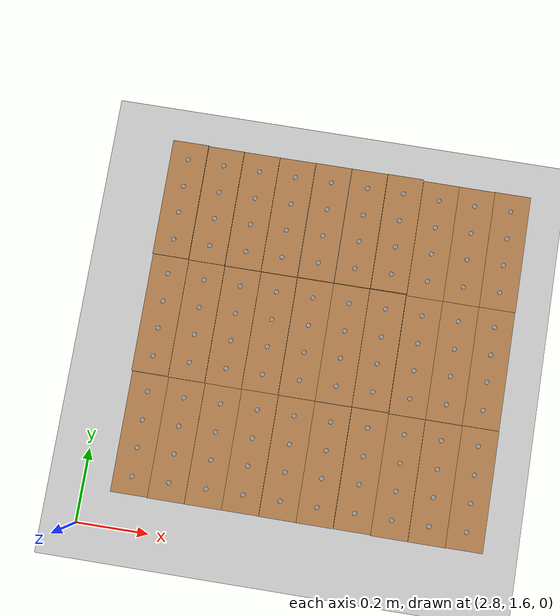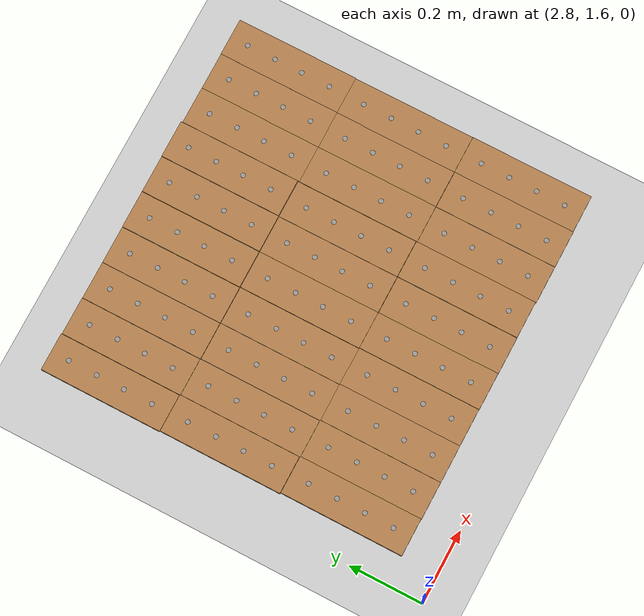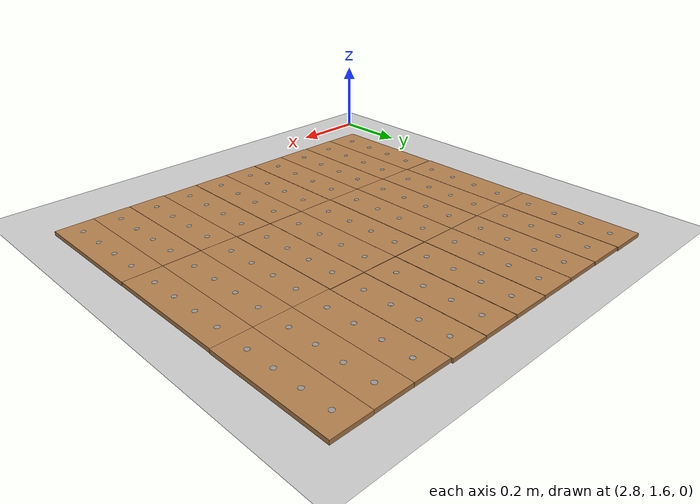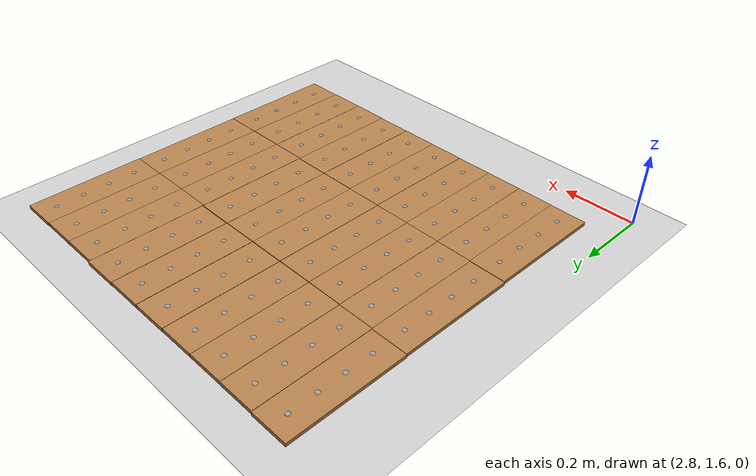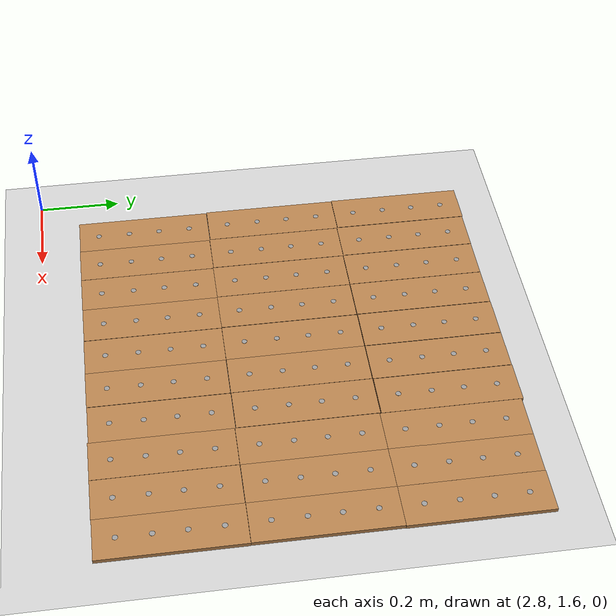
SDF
<sdf version="1.7">
 <world name="default">
  <light name="sun" type="directional">
   <pose>0 0 10 0 -0 0</pose>
   <diffuse>0.8 0.8 0.8 1</diffuse>
   <specular>0.2 0.2 0.2 1</specular>
   <attenuation>
    <range>1000</range>
    <constant>0.9</constant>
    <linear>0.01</linear>
    <quadratic>0.001</quadratic>
   </attenuation>
   <direction>-0.5 0.1 -0.9</direction>
   <spot><inner_angle>0</inner_angle><outer_angle>0</outer_angle><falloff>0</falloff></spot>
  </light>
  <model name="ground_plane">
   <static>1</static>
   <link name="link">
    <collision name="collision">
     <geometry><plane><normal>0 0 1</normal><size>100 100</size></plane></geometry>
     <surface><friction><ode><mu>100</mu><mu2>50</mu2></ode></friction></surface>
    </collision>
    <visual name="visual">
     <cast_shadows>0</cast_shadows>
     <geometry><plane><normal>0 0 1</normal><size>100 100</size></plane></geometry>
     <material>
      <script><uri>file://media/materials/scripts/gazebo.material</uri><name>Gazebo/Grey</name></script>
     </material>
    </visual>
   </link>
  </model>
  <gravity>0 0 -9.8</gravity>
  <magnetic_field>6e-06 2.3e-05 -4.2e-05</magnetic_field>
  <atmosphere type="adiabatic"/>
  <physics type="ode">
   <max_step_size>0.001</max_step_size>
   <real_time_factor>1</real_time_factor>
   <real_time_update_rate>1000</real_time_update_rate>
  </physics>
  <scene><ambient>0.4 0.4 0.4 1</ambient><background>0.7 0.7 0.7 1</background><shadows>1</shadows></scene>
  <spherical_coordinates>
   <surface_model>EARTH_WGS84</surface_model>
   <latitude_deg>0</latitude_deg>
   <longitude_deg>0</longitude_deg>
   <elevation>0</elevation>
   <heading_deg>0</heading_deg>
  </spherical_coordinates>
  <model name="wooden_board">
   <link name="base">
    <pose>0 0 0.00523 0 -0 0</pose>
    <inertial>
     <mass>0.2765</mass>
     <inertia>
      <ixx>0.0025148</ixx>
      <ixy>0</ixy>
      <ixz>0</ixz>
      <iyy>0.00024037</iyy>
      <iyz>0</iyz>
      <izz>0.00275013</izz>
     </inertia>
    </inertial>
    <collision name="collision">
     <geometry><box><size>0.1016 0.3302 0.01046</size></box></geometry>
     <surface>
      <contact>
       <poissons_ratio>0.347</poissons_ratio>
       <elastic_modulus>8.8e+09</elastic_modulus>
       <ode><kp>100000</kp><kd>100</kd><max_vel>100</max_vel><min_depth>0.001</min_depth></ode>
      </contact>
      <friction>
       <torsional>
        <coefficient>1</coefficient>
        <use_patch_radius>0</use_patch_radius>
        <surface_radius>0.01</surface_radius>
       </torsional>
      </friction>
     </surface>
    </collision>
    <visual name="visual">
     <geometry><box><size>0.1016 0.3302 0.01046</size></box></geometry>
     <material>
      <script><uri>file://media/materials/scripts/gazebo.material</uri><name>Gazebo/Wood</name></script>
     </material>
    </visual>
    <visual name="tee_nut_1">
     <pose>0 -0.116 0 0 -0 0</pose>
     <geometry><cylinder><radius>0.00635</radius><length>0.0105646</length></cylinder></geometry>
     <material>
      <script><uri>file://media/materials/scripts/gazebo.material</uri><name>Gazebo/Grey</name></script>
     </material>
    </visual>
    <visual name="tee_nut_2">
     <pose>0 -0.038 0 0 -0 0</pose>
     <geometry><cylinder><radius>0.00635</radius><length>0.0105646</length></cylinder></geometry>
     <material>
      <script><uri>file://media/materials/scripts/gazebo.material</uri><name>Gazebo/Grey</name></script>
     </material>
    </visual>
    <visual name="tee_nut_3">
     <pose>0 0.038 0 0 -0 0</pose>
     <geometry><cylinder><radius>0.00635</radius><length>0.0105646</length></cylinder></geometry>
     <material>
      <script><uri>file://media/materials/scripts/gazebo.material</uri><name>Gazebo/Grey</name></script>
     </material>
    </visual>
    <visual name="tee_nut_4">
     <pose>0 0.116 0 0 -0 0</pose>
     <geometry><cylinder><radius>0.00635</radius><length>0.0105646</length></cylinder></geometry>
     <material>
      <script><uri>file://media/materials/scripts/gazebo.material</uri><name>Gazebo/Grey</name></script>
     </material>
    </visual>
   </link>
   <pose>2.92931 1.86181 -0.001007 0 -0 -5.4e-05</pose>
  </model>
  <model name="wooden_board_clone">
   <link name="base">
    <pose>0 0 0.00523 0 -0 0</pose>
    <inertial>
     <mass>0.2765</mass>
     <inertia>
      <ixx>0.0025148</ixx>
      <ixy>0</ixy>
      <ixz>0</ixz>
      <iyy>0.00024037</iyy>
      <iyz>0</iyz>
      <izz>0.00275013</izz>
     </inertia>
    </inertial>
    <collision name="collision">
     <geometry><box><size>0.1016 0.3302 0.01046</size></box></geometry>
     <surface>
      <contact>
       <poissons_ratio>0.347</poissons_ratio>
       <elastic_modulus>8.8e+09</elastic_modulus>
       <ode><kp>100000</kp><kd>100</kd><max_vel>100</max_vel><min_depth>0.001</min_depth></ode>
      </contact>
      <friction>
       <torsional>
        <coefficient>1</coefficient>
        <use_patch_radius>0</use_patch_radius>
        <surface_radius>0.01</surface_radius>
       </torsional>
      </friction>
     </surface>
    </collision>
    <visual name="visual">
     <geometry><box><size>0.1016 0.3302 0.01046</size></box></geometry>
     <material>
      <script><uri>file://media/materials/scripts/gazebo.material</uri><name>Gazebo/Wood</name></script>
     </material>
    </visual>
    <visual name="tee_nut_1">
     <pose>0 -0.116 0 0 -0 0</pose>
     <geometry><cylinder><radius>0.00635</radius><length>0.0105646</length></cylinder></geometry>
     <material>
      <script><uri>file://media/materials/scripts/gazebo.material</uri><name>Gazebo/Grey</name></script>
     </material>
    </visual>
    <visual name="tee_nut_2">
     <pose>0 -0.038 0 0 -0 0</pose>
     <geometry><cylinder><radius>0.00635</radius><length>0.0105646</length></cylinder></geometry>
     <material>
      <script><uri>file://media/materials/scripts/gazebo.material</uri><name>Gazebo/Grey</name></script>
     </material>
    </visual>
    <visual name="tee_nut_3">
     <pose>0 0.038 0 0 -0 0</pose>
     <geometry><cylinder><radius>0.00635</radius><length>0.0105646</length></cylinder></geometry>
     <material>
      <script><uri>file://media/materials/scripts/gazebo.material</uri><name>Gazebo/Grey</name></script>
     </material>
    </visual>
    <visual name="tee_nut_4">
     <pose>0 0.116 0 0 -0 0</pose>
     <geometry><cylinder><radius>0.00635</radius><length>0.0105646</length></cylinder></geometry>
     <material>
      <script><uri>file://media/materials/scripts/gazebo.material</uri><name>Gazebo/Grey</name></script>
     </material>
    </visual>
   </link>
   <pose>3.03066 1.8608 -0.001007 -0 -0 -0</pose>
  </model>
  <model name="wooden_board_clone_0">
   <link name="base">
    <pose>0 0 0.00523 0 -0 0</pose>
    <inertial>
     <mass>0.2765</mass>
     <inertia>
      <ixx>0.0025148</ixx>
      <ixy>0</ixy>
      <ixz>0</ixz>
      <iyy>0.00024037</iyy>
      <iyz>0</iyz>
      <izz>0.00275013</izz>
     </inertia>
    </inertial>
    <collision name="collision">
     <geometry><box><size>0.1016 0.3302 0.01046</size></box></geometry>
     <surface>
      <contact>
       <poissons_ratio>0.347</poissons_ratio>
       <elastic_modulus>8.8e+09</elastic_modulus>
       <ode><kp>100000</kp><kd>100</kd><max_vel>100</max_vel><min_depth>0.001</min_depth></ode>
      </contact>
      <friction>
       <torsional>
        <coefficient>1</coefficient>
        <use_patch_radius>0</use_patch_radius>
        <surface_radius>0.01</surface_radius>
       </torsional>
      </friction>
     </surface>
    </collision>
    <visual name="visual">
     <geometry><box><size>0.1016 0.3302 0.01046</size></box></geometry>
     <material>
      <script><uri>file://media/materials/scripts/gazebo.material</uri><name>Gazebo/Wood</name></script>
     </material>
    </visual>
    <visual name="tee_nut_1">
     <pose>0 -0.116 0 0 -0 0</pose>
     <geometry><cylinder><radius>0.00635</radius><length>0.0105646</length></cylinder></geometry>
     <material>
      <script><uri>file://media/materials/scripts/gazebo.material</uri><name>Gazebo/Grey</name></script>
     </material>
    </visual>
    <visual name="tee_nut_2">
     <pose>0 -0.038 0 0 -0 0</pose>
     <geometry><cylinder><radius>0.00635</radius><length>0.0105646</length></cylinder></geometry>
     <material>
      <script><uri>file://media/materials/scripts/gazebo.material</uri><name>Gazebo/Grey</name></script>
     </material>
    </visual>
    <visual name="tee_nut_3">
     <pose>0 0.038 0 0 -0 0</pose>
     <geometry><cylinder><radius>0.00635</radius><length>0.0105646</length></cylinder></geometry>
     <material>
      <script><uri>file://media/materials/scripts/gazebo.material</uri><name>Gazebo/Grey</name></script>
     </material>
    </visual>
    <visual name="tee_nut_4">
     <pose>0 0.116 0 0 -0 0</pose>
     <geometry><cylinder><radius>0.00635</radius><length>0.0105646</length></cylinder></geometry>
     <material>
      <script><uri>file://media/materials/scripts/gazebo.material</uri><name>Gazebo/Grey</name></script>
     </material>
    </visual>
   </link>
   <pose>3.1325 1.86061 -0.001007 0 -0 0</pose>
  </model>
  <model name="wooden_board_clone_1">
   <link name="base">
    <pose>0 0 0.00523 0 -0 0</pose>
    <inertial>
     <mass>0.2765</mass>
     <inertia>
      <ixx>0.0025148</ixx>
      <ixy>0</ixy>
      <ixz>0</ixz>
      <iyy>0.00024037</iyy>
      <iyz>0</iyz>
      <izz>0.00275013</izz>
     </inertia>
    </inertial>
    <collision name="collision">
     <geometry><box><size>0.1016 0.3302 0.01046</size></box></geometry>
     <surface>
      <contact>
       <poissons_ratio>0.347</poissons_ratio>
       <elastic_modulus>8.8e+09</elastic_modulus>
       <ode><kp>100000</kp><kd>100</kd><max_vel>100</max_vel><min_depth>0.001</min_depth></ode>
      </contact>
      <friction>
       <torsional>
        <coefficient>1</coefficient>
        <use_patch_radius>0</use_patch_radius>
        <surface_radius>0.01</surface_radius>
       </torsional>
      </friction>
     </surface>
    </collision>
    <visual name="visual">
     <geometry><box><size>0.1016 0.3302 0.01046</size></box></geometry>
     <material>
      <script><uri>file://media/materials/scripts/gazebo.material</uri><name>Gazebo/Wood</name></script>
     </material>
    </visual>
    <visual name="tee_nut_1">
     <pose>0 -0.116 0 0 -0 0</pose>
     <geometry><cylinder><radius>0.00635</radius><length>0.0105646</length></cylinder></geometry>
     <material>
      <script><uri>file://media/materials/scripts/gazebo.material</uri><name>Gazebo/Grey</name></script>
     </material>
    </visual>
    <visual name="tee_nut_2">
     <pose>0 -0.038 0 0 -0 0</pose>
     <geometry><cylinder><radius>0.00635</radius><length>0.0105646</length></cylinder></geometry>
     <material>
      <script><uri>file://media/materials/scripts/gazebo.material</uri><name>Gazebo/Grey</name></script>
     </material>
    </visual>
    <visual name="tee_nut_3">
     <pose>0 0.038 0 0 -0 0</pose>
     <geometry><cylinder><radius>0.00635</radius><length>0.0105646</length></cylinder></geometry>
     <material>
      <script><uri>file://media/materials/scripts/gazebo.material</uri><name>Gazebo/Grey</name></script>
     </material>
    </visual>
    <visual name="tee_nut_4">
     <pose>0 0.116 0 0 -0 0</pose>
     <geometry><cylinder><radius>0.00635</radius><length>0.0105646</length></cylinder></geometry>
     <material>
      <script><uri>file://media/materials/scripts/gazebo.material</uri><name>Gazebo/Grey</name></script>
     </material>
    </visual>
   </link>
   <pose>3.23405 1.86073 -0.001007 -0 -0 -0</pose>
  </model>
  <model name="wooden_board_clone_2">
   <link name="base">
    <pose>0 0 0.00523 0 -0 0</pose>
    <inertial>
     <mass>0.2765</mass>
     <inertia>
      <ixx>0.0025148</ixx>
      <ixy>0</ixy>
      <ixz>0</ixz>
      <iyy>0.00024037</iyy>
      <iyz>0</iyz>
      <izz>0.00275013</izz>
     </inertia>
    </inertial>
    <collision name="collision">
     <geometry><box><size>0.1016 0.3302 0.01046</size></box></geometry>
     <surface>
      <contact>
       <poissons_ratio>0.347</poissons_ratio>
       <elastic_modulus>8.8e+09</elastic_modulus>
       <ode><kp>100000</kp><kd>100</kd><max_vel>100</max_vel><min_depth>0.001</min_depth></ode>
      </contact>
      <friction>
       <torsional>
        <coefficient>1</coefficient>
        <use_patch_radius>0</use_patch_radius>
        <surface_radius>0.01</surface_radius>
       </torsional>
      </friction>
     </surface>
    </collision>
    <visual name="visual">
     <geometry><box><size>0.1016 0.3302 0.01046</size></box></geometry>
     <material>
      <script><uri>file://media/materials/scripts/gazebo.material</uri><name>Gazebo/Wood</name></script>
     </material>
    </visual>
    <visual name="tee_nut_1">
     <pose>0 -0.116 0 0 -0 0</pose>
     <geometry><cylinder><radius>0.00635</radius><length>0.0105646</length></cylinder></geometry>
     <material>
      <script><uri>file://media/materials/scripts/gazebo.material</uri><name>Gazebo/Grey</name></script>
     </material>
    </visual>
    <visual name="tee_nut_2">
     <pose>0 -0.038 0 0 -0 0</pose>
     <geometry><cylinder><radius>0.00635</radius><length>0.0105646</length></cylinder></geometry>
     <material>
      <script><uri>file://media/materials/scripts/gazebo.material</uri><name>Gazebo/Grey</name></script>
     </material>
    </visual>
    <visual name="tee_nut_3">
     <pose>0 0.038 0 0 -0 0</pose>
     <geometry><cylinder><radius>0.00635</radius><length>0.0105646</length></cylinder></geometry>
     <material>
      <script><uri>file://media/materials/scripts/gazebo.material</uri><name>Gazebo/Grey</name></script>
     </material>
    </visual>
    <visual name="tee_nut_4">
     <pose>0 0.116 0 0 -0 0</pose>
     <geometry><cylinder><radius>0.00635</radius><length>0.0105646</length></cylinder></geometry>
     <material>
      <script><uri>file://media/materials/scripts/gazebo.material</uri><name>Gazebo/Grey</name></script>
     </material>
    </visual>
   </link>
   <pose>3.33629 1.86003 -0.001007 0 -0 0</pose>
  </model>
  <model name="wooden_board_clone_3">
   <link name="base">
    <pose>0 0 0.00523 0 -0 0</pose>
    <inertial>
     <mass>0.2765</mass>
     <inertia>
      <ixx>0.0025148</ixx>
      <ixy>0</ixy>
      <ixz>0</ixz>
      <iyy>0.00024037</iyy>
      <iyz>0</iyz>
      <izz>0.00275013</izz>
     </inertia>
    </inertial>
    <collision name="collision">
     <geometry><box><size>0.1016 0.3302 0.01046</size></box></geometry>
     <surface>
      <contact>
       <poissons_ratio>0.347</poissons_ratio>
       <elastic_modulus>8.8e+09</elastic_modulus>
       <ode><kp>100000</kp><kd>100</kd><max_vel>100</max_vel><min_depth>0.001</min_depth></ode>
      </contact>
      <friction>
       <torsional>
        <coefficient>1</coefficient>
        <use_patch_radius>0</use_patch_radius>
        <surface_radius>0.01</surface_radius>
       </torsional>
      </friction>
     </surface>
    </collision>
    <visual name="visual">
     <geometry><box><size>0.1016 0.3302 0.01046</size></box></geometry>
     <material>
      <script><uri>file://media/materials/scripts/gazebo.material</uri><name>Gazebo/Wood</name></script>
     </material>
    </visual>
    <visual name="tee_nut_1">
     <pose>0 -0.116 0 0 -0 0</pose>
     <geometry><cylinder><radius>0.00635</radius><length>0.0105646</length></cylinder></geometry>
     <material>
      <script><uri>file://media/materials/scripts/gazebo.material</uri><name>Gazebo/Grey</name></script>
     </material>
    </visual>
    <visual name="tee_nut_2">
     <pose>0 -0.038 0 0 -0 0</pose>
     <geometry><cylinder><radius>0.00635</radius><length>0.0105646</length></cylinder></geometry>
     <material>
      <script><uri>file://media/materials/scripts/gazebo.material</uri><name>Gazebo/Grey</name></script>
     </material>
    </visual>
    <visual name="tee_nut_3">
     <pose>0 0.038 0 0 -0 0</pose>
     <geometry><cylinder><radius>0.00635</radius><length>0.0105646</length></cylinder></geometry>
     <material>
      <script><uri>file://media/materials/scripts/gazebo.material</uri><name>Gazebo/Grey</name></script>
     </material>
    </visual>
    <visual name="tee_nut_4">
     <pose>0 0.116 0 0 -0 0</pose>
     <geometry><cylinder><radius>0.00635</radius><length>0.0105646</length></cylinder></geometry>
     <material>
      <script><uri>file://media/materials/scripts/gazebo.material</uri><name>Gazebo/Grey</name></script>
     </material>
    </visual>
   </link>
   <pose>3.4371 1.85953 -0.001007 0 -0 1e-06</pose>
  </model>
  <model name="wooden_board_clone_5">
   <link name="base">
    <pose>0 0 0.00523 0 -0 0</pose>
    <inertial>
     <mass>0.2765</mass>
     <inertia>
      <ixx>0.0025148</ixx>
      <ixy>0</ixy>
      <ixz>0</ixz>
      <iyy>0.00024037</iyy>
      <iyz>0</iyz>
      <izz>0.00275013</izz>
     </inertia>
    </inertial>
    <collision name="collision">
     <geometry><box><size>0.1016 0.3302 0.01046</size></box></geometry>
     <surface>
      <contact>
       <poissons_ratio>0.347</poissons_ratio>
       <elastic_modulus>8.8e+09</elastic_modulus>
       <ode><kp>100000</kp><kd>100</kd><max_vel>100</max_vel><min_depth>0.001</min_depth></ode>
      </contact>
      <friction>
       <torsional>
        <coefficient>1</coefficient>
        <use_patch_radius>0</use_patch_radius>
        <surface_radius>0.01</surface_radius>
       </torsional>
      </friction>
     </surface>
    </collision>
    <visual name="visual">
     <geometry><box><size>0.1016 0.3302 0.01046</size></box></geometry>
     <material>
      <script><uri>file://media/materials/scripts/gazebo.material</uri><name>Gazebo/Wood</name></script>
     </material>
    </visual>
    <visual name="tee_nut_1">
     <pose>0 -0.116 0 0 -0 0</pose>
     <geometry><cylinder><radius>0.00635</radius><length>0.0105646</length></cylinder></geometry>
     <material>
      <script><uri>file://media/materials/scripts/gazebo.material</uri><name>Gazebo/Grey</name></script>
     </material>
    </visual>
    <visual name="tee_nut_2">
     <pose>0 -0.038 0 0 -0 0</pose>
     <geometry><cylinder><radius>0.00635</radius><length>0.0105646</length></cylinder></geometry>
     <material>
      <script><uri>file://media/materials/scripts/gazebo.material</uri><name>Gazebo/Grey</name></script>
     </material>
    </visual>
    <visual name="tee_nut_3">
     <pose>0 0.038 0 0 -0 0</pose>
     <geometry><cylinder><radius>0.00635</radius><length>0.0105646</length></cylinder></geometry>
     <material>
      <script><uri>file://media/materials/scripts/gazebo.material</uri><name>Gazebo/Grey</name></script>
     </material>
    </visual>
    <visual name="tee_nut_4">
     <pose>0 0.116 0 0 -0 0</pose>
     <geometry><cylinder><radius>0.00635</radius><length>0.0105646</length></cylinder></geometry>
     <material>
      <script><uri>file://media/materials/scripts/gazebo.material</uri><name>Gazebo/Grey</name></script>
     </material>
    </visual>
   </link>
   <pose>3.64062 1.85795 -0.001007 0 -0 0</pose>
  </model>
  <model name="wooden_board_clone_6">
   <link name="base">
    <pose>0 0 0.00523 0 -0 0</pose>
    <inertial>
     <mass>0.2765</mass>
     <inertia>
      <ixx>0.0025148</ixx>
      <ixy>0</ixy>
      <ixz>0</ixz>
      <iyy>0.00024037</iyy>
      <iyz>0</iyz>
      <izz>0.00275013</izz>
     </inertia>
    </inertial>
    <collision name="collision">
     <geometry><box><size>0.1016 0.3302 0.01046</size></box></geometry>
     <surface>
      <contact>
       <poissons_ratio>0.347</poissons_ratio>
       <elastic_modulus>8.8e+09</elastic_modulus>
       <ode><kp>100000</kp><kd>100</kd><max_vel>100</max_vel><min_depth>0.001</min_depth></ode>
      </contact>
      <friction>
       <torsional>
        <coefficient>1</coefficient>
        <use_patch_radius>0</use_patch_radius>
        <surface_radius>0.01</surface_radius>
       </torsional>
      </friction>
     </surface>
    </collision>
    <visual name="visual">
     <geometry><box><size>0.1016 0.3302 0.01046</size></box></geometry>
     <material>
      <script><uri>file://media/materials/scripts/gazebo.material</uri><name>Gazebo/Wood</name></script>
     </material>
    </visual>
    <visual name="tee_nut_1">
     <pose>0 -0.116 0 0 -0 0</pose>
     <geometry><cylinder><radius>0.00635</radius><length>0.0105646</length></cylinder></geometry>
     <material>
      <script><uri>file://media/materials/scripts/gazebo.material</uri><name>Gazebo/Grey</name></script>
     </material>
    </visual>
    <visual name="tee_nut_2">
     <pose>0 -0.038 0 0 -0 0</pose>
     <geometry><cylinder><radius>0.00635</radius><length>0.0105646</length></cylinder></geometry>
     <material>
      <script><uri>file://media/materials/scripts/gazebo.material</uri><name>Gazebo/Grey</name></script>
     </material>
    </visual>
    <visual name="tee_nut_3">
     <pose>0 0.038 0 0 -0 0</pose>
     <geometry><cylinder><radius>0.00635</radius><length>0.0105646</length></cylinder></geometry>
     <material>
      <script><uri>file://media/materials/scripts/gazebo.material</uri><name>Gazebo/Grey</name></script>
     </material>
    </visual>
    <visual name="tee_nut_4">
     <pose>0 0.116 0 0 -0 0</pose>
     <geometry><cylinder><radius>0.00635</radius><length>0.0105646</length></cylinder></geometry>
     <material>
      <script><uri>file://media/materials/scripts/gazebo.material</uri><name>Gazebo/Grey</name></script>
     </material>
    </visual>
   </link>
   <pose>3.74259 1.85781 -0.001007 0 -0 0</pose>
  </model>
  <model name="wooden_board_clone_7">
   <link name="base">
    <pose>0 0 0.00523 0 -0 0</pose>
    <inertial>
     <mass>0.2765</mass>
     <inertia>
      <ixx>0.0025148</ixx>
      <ixy>0</ixy>
      <ixz>0</ixz>
      <iyy>0.00024037</iyy>
      <iyz>0</iyz>
      <izz>0.00275013</izz>
     </inertia>
    </inertial>
    <collision name="collision">
     <geometry><box><size>0.1016 0.3302 0.01046</size></box></geometry>
     <surface>
      <contact>
       <poissons_ratio>0.347</poissons_ratio>
       <elastic_modulus>8.8e+09</elastic_modulus>
       <ode><kp>100000</kp><kd>100</kd><max_vel>100</max_vel><min_depth>0.001</min_depth></ode>
      </contact>
      <friction>
       <torsional>
        <coefficient>1</coefficient>
        <use_patch_radius>0</use_patch_radius>
        <surface_radius>0.01</surface_radius>
       </torsional>
      </friction>
     </surface>
    </collision>
    <visual name="visual">
     <geometry><box><size>0.1016 0.3302 0.01046</size></box></geometry>
     <material>
      <script><uri>file://media/materials/scripts/gazebo.material</uri><name>Gazebo/Wood</name></script>
     </material>
    </visual>
    <visual name="tee_nut_1">
     <pose>0 -0.116 0 0 -0 0</pose>
     <geometry><cylinder><radius>0.00635</radius><length>0.0105646</length></cylinder></geometry>
     <material>
      <script><uri>file://media/materials/scripts/gazebo.material</uri><name>Gazebo/Grey</name></script>
     </material>
    </visual>
    <visual name="tee_nut_2">
     <pose>0 -0.038 0 0 -0 0</pose>
     <geometry><cylinder><radius>0.00635</radius><length>0.0105646</length></cylinder></geometry>
     <material>
      <script><uri>file://media/materials/scripts/gazebo.material</uri><name>Gazebo/Grey</name></script>
     </material>
    </visual>
    <visual name="tee_nut_3">
     <pose>0 0.038 0 0 -0 0</pose>
     <geometry><cylinder><radius>0.00635</radius><length>0.0105646</length></cylinder></geometry>
     <material>
      <script><uri>file://media/materials/scripts/gazebo.material</uri><name>Gazebo/Grey</name></script>
     </material>
    </visual>
    <visual name="tee_nut_4">
     <pose>0 0.116 0 0 -0 0</pose>
     <geometry><cylinder><radius>0.00635</radius><length>0.0105646</length></cylinder></geometry>
     <material>
      <script><uri>file://media/materials/scripts/gazebo.material</uri><name>Gazebo/Grey</name></script>
     </material>
    </visual>
   </link>
   <pose>3.84384 1.85854 -0.001007 0 -0 0</pose>
  </model>
  <model name="wooden_board_clone_8">
   <link name="base">
    <pose>0 0 0.00523 0 -0 0</pose>
    <inertial>
     <mass>0.2765</mass>
     <inertia>
      <ixx>0.0025148</ixx>
      <ixy>0</ixy>
      <ixz>0</ixz>
      <iyy>0.00024037</iyy>
      <iyz>0</iyz>
      <izz>0.00275013</izz>
     </inertia>
    </inertial>
    <collision name="collision">
     <geometry><box><size>0.1016 0.3302 0.01046</size></box></geometry>
     <surface>
      <contact>
       <poissons_ratio>0.347</poissons_ratio>
       <elastic_modulus>8.8e+09</elastic_modulus>
       <ode><kp>100000</kp><kd>100</kd><max_vel>100</max_vel><min_depth>0.001</min_depth></ode>
      </contact>
      <friction>
       <torsional>
        <coefficient>1</coefficient>
        <use_patch_radius>0</use_patch_radius>
        <surface_radius>0.01</surface_radius>
       </torsional>
      </friction>
     </surface>
    </collision>
    <visual name="visual">
     <geometry><box><size>0.1016 0.3302 0.01046</size></box></geometry>
     <material>
      <script><uri>file://media/materials/scripts/gazebo.material</uri><name>Gazebo/Wood</name></script>
     </material>
    </visual>
    <visual name="tee_nut_1">
     <pose>0 -0.116 0 0 -0 0</pose>
     <geometry><cylinder><radius>0.00635</radius><length>0.0105646</length></cylinder></geometry>
     <material>
      <script><uri>file://media/materials/scripts/gazebo.material</uri><name>Gazebo/Grey</name></script>
     </material>
    </visual>
    <visual name="tee_nut_2">
     <pose>0 -0.038 0 0 -0 0</pose>
     <geometry><cylinder><radius>0.00635</radius><length>0.0105646</length></cylinder></geometry>
     <material>
      <script><uri>file://media/materials/scripts/gazebo.material</uri><name>Gazebo/Grey</name></script>
     </material>
    </visual>
    <visual name="tee_nut_3">
     <pose>0 0.038 0 0 -0 0</pose>
     <geometry><cylinder><radius>0.00635</radius><length>0.0105646</length></cylinder></geometry>
     <material>
      <script><uri>file://media/materials/scripts/gazebo.material</uri><name>Gazebo/Grey</name></script>
     </material>
    </visual>
    <visual name="tee_nut_4">
     <pose>0 0.116 0 0 -0 0</pose>
     <geometry><cylinder><radius>0.00635</radius><length>0.0105646</length></cylinder></geometry>
     <material>
      <script><uri>file://media/materials/scripts/gazebo.material</uri><name>Gazebo/Grey</name></script>
     </material>
    </visual>
   </link>
   <pose>3.84334 2.18906 -0.001007 0 -0 0</pose>
  </model>
  <model name="wooden_board_clone_9">
   <link name="base">
    <pose>0 0 0.00523 0 -0 0</pose>
    <inertial>
     <mass>0.2765</mass>
     <inertia>
      <ixx>0.0025148</ixx>
      <ixy>0</ixy>
      <ixz>0</ixz>
      <iyy>0.00024037</iyy>
      <iyz>0</iyz>
      <izz>0.00275013</izz>
     </inertia>
    </inertial>
    <collision name="collision">
     <geometry><box><size>0.1016 0.3302 0.01046</size></box></geometry>
     <surface>
      <contact>
       <poissons_ratio>0.347</poissons_ratio>
       <elastic_modulus>8.8e+09</elastic_modulus>
       <ode><kp>100000</kp><kd>100</kd><max_vel>100</max_vel><min_depth>0.001</min_depth></ode>
      </contact>
      <friction>
       <torsional>
        <coefficient>1</coefficient>
        <use_patch_radius>0</use_patch_radius>
        <surface_radius>0.01</surface_radius>
       </torsional>
      </friction>
     </surface>
    </collision>
    <visual name="visual">
     <geometry><box><size>0.1016 0.3302 0.01046</size></box></geometry>
     <material>
      <script><uri>file://media/materials/scripts/gazebo.material</uri><name>Gazebo/Wood</name></script>
     </material>
    </visual>
    <visual name="tee_nut_1">
     <pose>0 -0.116 0 0 -0 0</pose>
     <geometry><cylinder><radius>0.00635</radius><length>0.0105646</length></cylinder></geometry>
     <material>
      <script><uri>file://media/materials/scripts/gazebo.material</uri><name>Gazebo/Grey</name></script>
     </material>
    </visual>
    <visual name="tee_nut_2">
     <pose>0 -0.038 0 0 -0 0</pose>
     <geometry><cylinder><radius>0.00635</radius><length>0.0105646</length></cylinder></geometry>
     <material>
      <script><uri>file://media/materials/scripts/gazebo.material</uri><name>Gazebo/Grey</name></script>
     </material>
    </visual>
    <visual name="tee_nut_3">
     <pose>0 0.038 0 0 -0 0</pose>
     <geometry><cylinder><radius>0.00635</radius><length>0.0105646</length></cylinder></geometry>
     <material>
      <script><uri>file://media/materials/scripts/gazebo.material</uri><name>Gazebo/Grey</name></script>
     </material>
    </visual>
    <visual name="tee_nut_4">
     <pose>0 0.116 0 0 -0 0</pose>
     <geometry><cylinder><radius>0.00635</radius><length>0.0105646</length></cylinder></geometry>
     <material>
      <script><uri>file://media/materials/scripts/gazebo.material</uri><name>Gazebo/Grey</name></script>
     </material>
    </visual>
   </link>
   <pose>3.74249 2.18883 -0.001007 0 -0 0</pose>
  </model>
  <model name="wooden_board_clone_10">
   <link name="base">
    <pose>0 0 0.00523 0 -0 0</pose>
    <inertial>
     <mass>0.2765</mass>
     <inertia>
      <ixx>0.0025148</ixx>
      <ixy>0</ixy>
      <ixz>0</ixz>
      <iyy>0.00024037</iyy>
      <iyz>0</iyz>
      <izz>0.00275013</izz>
     </inertia>
    </inertial>
    <collision name="collision">
     <geometry><box><size>0.1016 0.3302 0.01046</size></box></geometry>
     <surface>
      <contact>
       <poissons_ratio>0.347</poissons_ratio>
       <elastic_modulus>8.8e+09</elastic_modulus>
       <ode><kp>100000</kp><kd>100</kd><max_vel>100</max_vel><min_depth>0.001</min_depth></ode>
      </contact>
      <friction>
       <torsional>
        <coefficient>1</coefficient>
        <use_patch_radius>0</use_patch_radius>
        <surface_radius>0.01</surface_radius>
       </torsional>
      </friction>
     </surface>
    </collision>
    <visual name="visual">
     <geometry><box><size>0.1016 0.3302 0.01046</size></box></geometry>
     <material>
      <script><uri>file://media/materials/scripts/gazebo.material</uri><name>Gazebo/Wood</name></script>
     </material>
    </visual>
    <visual name="tee_nut_1">
     <pose>0 -0.116 0 0 -0 0</pose>
     <geometry><cylinder><radius>0.00635</radius><length>0.0105646</length></cylinder></geometry>
     <material>
      <script><uri>file://media/materials/scripts/gazebo.material</uri><name>Gazebo/Grey</name></script>
     </material>
    </visual>
    <visual name="tee_nut_2">
     <pose>0 -0.038 0 0 -0 0</pose>
     <geometry><cylinder><radius>0.00635</radius><length>0.0105646</length></cylinder></geometry>
     <material>
      <script><uri>file://media/materials/scripts/gazebo.material</uri><name>Gazebo/Grey</name></script>
     </material>
    </visual>
    <visual name="tee_nut_3">
     <pose>0 0.038 0 0 -0 0</pose>
     <geometry><cylinder><radius>0.00635</radius><length>0.0105646</length></cylinder></geometry>
     <material>
      <script><uri>file://media/materials/scripts/gazebo.material</uri><name>Gazebo/Grey</name></script>
     </material>
    </visual>
    <visual name="tee_nut_4">
     <pose>0 0.116 0 0 -0 0</pose>
     <geometry><cylinder><radius>0.00635</radius><length>0.0105646</length></cylinder></geometry>
     <material>
      <script><uri>file://media/materials/scripts/gazebo.material</uri><name>Gazebo/Grey</name></script>
     </material>
    </visual>
   </link>
   <pose>3.64116 2.18846 -0.001007 0 -0 0</pose>
  </model>
  <model name="wooden_board_clone_12">
   <link name="base">
    <pose>0 0 0.00523 0 -0 0</pose>
    <inertial>
     <mass>0.2765</mass>
     <inertia>
      <ixx>0.0025148</ixx>
      <ixy>0</ixy>
      <ixz>0</ixz>
      <iyy>0.00024037</iyy>
      <iyz>0</iyz>
      <izz>0.00275013</izz>
     </inertia>
    </inertial>
    <collision name="collision">
     <geometry><box><size>0.1016 0.3302 0.01046</size></box></geometry>
     <surface>
      <contact>
       <poissons_ratio>0.347</poissons_ratio>
       <elastic_modulus>8.8e+09</elastic_modulus>
       <ode><kp>100000</kp><kd>100</kd><max_vel>100</max_vel><min_depth>0.001</min_depth></ode>
      </contact>
      <friction>
       <torsional>
        <coefficient>1</coefficient>
        <use_patch_radius>0</use_patch_radius>
        <surface_radius>0.01</surface_radius>
       </torsional>
      </friction>
     </surface>
    </collision>
    <visual name="visual">
     <geometry><box><size>0.1016 0.3302 0.01046</size></box></geometry>
     <material>
      <script><uri>file://media/materials/scripts/gazebo.material</uri><name>Gazebo/Wood</name></script>
     </material>
    </visual>
    <visual name="tee_nut_1">
     <pose>0 -0.116 0 0 -0 0</pose>
     <geometry><cylinder><radius>0.00635</radius><length>0.0105646</length></cylinder></geometry>
     <material>
      <script><uri>file://media/materials/scripts/gazebo.material</uri><name>Gazebo/Grey</name></script>
     </material>
    </visual>
    <visual name="tee_nut_2">
     <pose>0 -0.038 0 0 -0 0</pose>
     <geometry><cylinder><radius>0.00635</radius><length>0.0105646</length></cylinder></geometry>
     <material>
      <script><uri>file://media/materials/scripts/gazebo.material</uri><name>Gazebo/Grey</name></script>
     </material>
    </visual>
    <visual name="tee_nut_3">
     <pose>0 0.038 0 0 -0 0</pose>
     <geometry><cylinder><radius>0.00635</radius><length>0.0105646</length></cylinder></geometry>
     <material>
      <script><uri>file://media/materials/scripts/gazebo.material</uri><name>Gazebo/Grey</name></script>
     </material>
    </visual>
    <visual name="tee_nut_4">
     <pose>0 0.116 0 0 -0 0</pose>
     <geometry><cylinder><radius>0.00635</radius><length>0.0105646</length></cylinder></geometry>
     <material>
      <script><uri>file://media/materials/scripts/gazebo.material</uri><name>Gazebo/Grey</name></script>
     </material>
    </visual>
   </link>
   <pose>3.43684 2.19065 -0.001007 0 -0 0</pose>
  </model>
  <model name="wooden_board_clone_13">
   <link name="base">
    <pose>0 0 0.00523 0 -0 0</pose>
    <inertial>
     <mass>0.2765</mass>
     <inertia>
      <ixx>0.0025148</ixx>
      <ixy>0</ixy>
      <ixz>0</ixz>
      <iyy>0.00024037</iyy>
      <iyz>0</iyz>
      <izz>0.00275013</izz>
     </inertia>
    </inertial>
    <collision name="collision">
     <geometry><box><size>0.1016 0.3302 0.01046</size></box></geometry>
     <surface>
      <contact>
       <poissons_ratio>0.347</poissons_ratio>
       <elastic_modulus>8.8e+09</elastic_modulus>
       <ode><kp>100000</kp><kd>100</kd><max_vel>100</max_vel><min_depth>0.001</min_depth></ode>
      </contact>
      <friction>
       <torsional>
        <coefficient>1</coefficient>
        <use_patch_radius>0</use_patch_radius>
        <surface_radius>0.01</surface_radius>
       </torsional>
      </friction>
     </surface>
    </collision>
    <visual name="visual">
     <geometry><box><size>0.1016 0.3302 0.01046</size></box></geometry>
     <material>
      <script><uri>file://media/materials/scripts/gazebo.material</uri><name>Gazebo/Wood</name></script>
     </material>
    </visual>
    <visual name="tee_nut_1">
     <pose>0 -0.116 0 0 -0 0</pose>
     <geometry><cylinder><radius>0.00635</radius><length>0.0105646</length></cylinder></geometry>
     <material>
      <script><uri>file://media/materials/scripts/gazebo.material</uri><name>Gazebo/Grey</name></script>
     </material>
    </visual>
    <visual name="tee_nut_2">
     <pose>0 -0.038 0 0 -0 0</pose>
     <geometry><cylinder><radius>0.00635</radius><length>0.0105646</length></cylinder></geometry>
     <material>
      <script><uri>file://media/materials/scripts/gazebo.material</uri><name>Gazebo/Grey</name></script>
     </material>
    </visual>
    <visual name="tee_nut_3">
     <pose>0 0.038 0 0 -0 0</pose>
     <geometry><cylinder><radius>0.00635</radius><length>0.0105646</length></cylinder></geometry>
     <material>
      <script><uri>file://media/materials/scripts/gazebo.material</uri><name>Gazebo/Grey</name></script>
     </material>
    </visual>
    <visual name="tee_nut_4">
     <pose>0 0.116 0 0 -0 0</pose>
     <geometry><cylinder><radius>0.00635</radius><length>0.0105646</length></cylinder></geometry>
     <material>
      <script><uri>file://media/materials/scripts/gazebo.material</uri><name>Gazebo/Grey</name></script>
     </material>
    </visual>
   </link>
   <pose>3.33522 2.19045 -0.001007 0 -0 0</pose>
  </model>
  <model name="wooden_board_clone_14">
   <link name="base">
    <pose>0 0 0.00523 0 -0 0</pose>
    <inertial>
     <mass>0.2765</mass>
     <inertia>
      <ixx>0.0025148</ixx>
      <ixy>0</ixy>
      <ixz>0</ixz>
      <iyy>0.00024037</iyy>
      <iyz>0</iyz>
      <izz>0.00275013</izz>
     </inertia>
    </inertial>
    <collision name="collision">
     <geometry><box><size>0.1016 0.3302 0.01046</size></box></geometry>
     <surface>
      <contact>
       <poissons_ratio>0.347</poissons_ratio>
       <elastic_modulus>8.8e+09</elastic_modulus>
       <ode><kp>100000</kp><kd>100</kd><max_vel>100</max_vel><min_depth>0.001</min_depth></ode>
      </contact>
      <friction>
       <torsional>
        <coefficient>1</coefficient>
        <use_patch_radius>0</use_patch_radius>
        <surface_radius>0.01</surface_radius>
       </torsional>
      </friction>
     </surface>
    </collision>
    <visual name="visual">
     <geometry><box><size>0.1016 0.3302 0.01046</size></box></geometry>
     <material>
      <script><uri>file://media/materials/scripts/gazebo.material</uri><name>Gazebo/Wood</name></script>
     </material>
    </visual>
    <visual name="tee_nut_1">
     <pose>0 -0.116 0 0 -0 0</pose>
     <geometry><cylinder><radius>0.00635</radius><length>0.0105646</length></cylinder></geometry>
     <material>
      <script><uri>file://media/materials/scripts/gazebo.material</uri><name>Gazebo/Grey</name></script>
     </material>
    </visual>
    <visual name="tee_nut_2">
     <pose>0 -0.038 0 0 -0 0</pose>
     <geometry><cylinder><radius>0.00635</radius><length>0.0105646</length></cylinder></geometry>
     <material>
      <script><uri>file://media/materials/scripts/gazebo.material</uri><name>Gazebo/Grey</name></script>
     </material>
    </visual>
    <visual name="tee_nut_3">
     <pose>0 0.038 0 0 -0 0</pose>
     <geometry><cylinder><radius>0.00635</radius><length>0.0105646</length></cylinder></geometry>
     <material>
      <script><uri>file://media/materials/scripts/gazebo.material</uri><name>Gazebo/Grey</name></script>
     </material>
    </visual>
    <visual name="tee_nut_4">
     <pose>0 0.116 0 0 -0 0</pose>
     <geometry><cylinder><radius>0.00635</radius><length>0.0105646</length></cylinder></geometry>
     <material>
      <script><uri>file://media/materials/scripts/gazebo.material</uri><name>Gazebo/Grey</name></script>
     </material>
    </visual>
   </link>
   <pose>3.23269 2.19005 -0.001007 0 -0 0</pose>
  </model>
  <model name="wooden_board_clone_15">
   <link name="base">
    <pose>0 0 0.00523 0 -0 0</pose>
    <inertial>
     <mass>0.2765</mass>
     <inertia>
      <ixx>0.0025148</ixx>
      <ixy>0</ixy>
      <ixz>0</ixz>
      <iyy>0.00024037</iyy>
      <iyz>0</iyz>
      <izz>0.00275013</izz>
     </inertia>
    </inertial>
    <collision name="collision">
     <geometry><box><size>0.1016 0.3302 0.01046</size></box></geometry>
     <surface>
      <contact>
       <poissons_ratio>0.347</poissons_ratio>
       <elastic_modulus>8.8e+09</elastic_modulus>
       <ode><kp>100000</kp><kd>100</kd><max_vel>100</max_vel><min_depth>0.001</min_depth></ode>
      </contact>
      <friction>
       <torsional>
        <coefficient>1</coefficient>
        <use_patch_radius>0</use_patch_radius>
        <surface_radius>0.01</surface_radius>
       </torsional>
      </friction>
     </surface>
    </collision>
    <visual name="visual">
     <geometry><box><size>0.1016 0.3302 0.01046</size></box></geometry>
     <material>
      <script><uri>file://media/materials/scripts/gazebo.material</uri><name>Gazebo/Wood</name></script>
     </material>
    </visual>
    <visual name="tee_nut_1">
     <pose>0 -0.116 0 0 -0 0</pose>
     <geometry><cylinder><radius>0.00635</radius><length>0.0105646</length></cylinder></geometry>
     <material>
      <script><uri>file://media/materials/scripts/gazebo.material</uri><name>Gazebo/Grey</name></script>
     </material>
    </visual>
    <visual name="tee_nut_2">
     <pose>0 -0.038 0 0 -0 0</pose>
     <geometry><cylinder><radius>0.00635</radius><length>0.0105646</length></cylinder></geometry>
     <material>
      <script><uri>file://media/materials/scripts/gazebo.material</uri><name>Gazebo/Grey</name></script>
     </material>
    </visual>
    <visual name="tee_nut_3">
     <pose>0 0.038 0 0 -0 0</pose>
     <geometry><cylinder><radius>0.00635</radius><length>0.0105646</length></cylinder></geometry>
     <material>
      <script><uri>file://media/materials/scripts/gazebo.material</uri><name>Gazebo/Grey</name></script>
     </material>
    </visual>
    <visual name="tee_nut_4">
     <pose>0 0.116 0 0 -0 0</pose>
     <geometry><cylinder><radius>0.00635</radius><length>0.0105646</length></cylinder></geometry>
     <material>
      <script><uri>file://media/materials/scripts/gazebo.material</uri><name>Gazebo/Grey</name></script>
     </material>
    </visual>
   </link>
   <pose>3.13073 2.19028 -0.001007 -0 -0 -0</pose>
  </model>
  <model name="wooden_board_clone_16">
   <link name="base">
    <pose>0 0 0.00523 0 -0 0</pose>
    <inertial>
     <mass>0.2765</mass>
     <inertia>
      <ixx>0.0025148</ixx>
      <ixy>0</ixy>
      <ixz>0</ixz>
      <iyy>0.00024037</iyy>
      <iyz>0</iyz>
      <izz>0.00275013</izz>
     </inertia>
    </inertial>
    <collision name="collision">
     <geometry><box><size>0.1016 0.3302 0.01046</size></box></geometry>
     <surface>
      <contact>
       <poissons_ratio>0.347</poissons_ratio>
       <elastic_modulus>8.8e+09</elastic_modulus>
       <ode><kp>100000</kp><kd>100</kd><max_vel>100</max_vel><min_depth>0.001</min_depth></ode>
      </contact>
      <friction>
       <torsional>
        <coefficient>1</coefficient>
        <use_patch_radius>0</use_patch_radius>
        <surface_radius>0.01</surface_radius>
       </torsional>
      </friction>
     </surface>
    </collision>
    <visual name="visual">
     <geometry><box><size>0.1016 0.3302 0.01046</size></box></geometry>
     <material>
      <script><uri>file://media/materials/scripts/gazebo.material</uri><name>Gazebo/Wood</name></script>
     </material>
    </visual>
    <visual name="tee_nut_1">
     <pose>0 -0.116 0 0 -0 0</pose>
     <geometry><cylinder><radius>0.00635</radius><length>0.0105646</length></cylinder></geometry>
     <material>
      <script><uri>file://media/materials/scripts/gazebo.material</uri><name>Gazebo/Grey</name></script>
     </material>
    </visual>
    <visual name="tee_nut_2">
     <pose>0 -0.038 0 0 -0 0</pose>
     <geometry><cylinder><radius>0.00635</radius><length>0.0105646</length></cylinder></geometry>
     <material>
      <script><uri>file://media/materials/scripts/gazebo.material</uri><name>Gazebo/Grey</name></script>
     </material>
    </visual>
    <visual name="tee_nut_3">
     <pose>0 0.038 0 0 -0 0</pose>
     <geometry><cylinder><radius>0.00635</radius><length>0.0105646</length></cylinder></geometry>
     <material>
      <script><uri>file://media/materials/scripts/gazebo.material</uri><name>Gazebo/Grey</name></script>
     </material>
    </visual>
    <visual name="tee_nut_4">
     <pose>0 0.116 0 0 -0 0</pose>
     <geometry><cylinder><radius>0.00635</radius><length>0.0105646</length></cylinder></geometry>
     <material>
      <script><uri>file://media/materials/scripts/gazebo.material</uri><name>Gazebo/Grey</name></script>
     </material>
    </visual>
   </link>
   <pose>3.02857 2.19129 -0.001007 0 -0 -5.5e-05</pose>
  </model>
  <model name="wooden_board_clone_17">
   <link name="base">
    <pose>0 0 0.00523 0 -0 0</pose>
    <inertial>
     <mass>0.2765</mass>
     <inertia>
      <ixx>0.0025148</ixx>
      <ixy>0</ixy>
      <ixz>0</ixz>
      <iyy>0.00024037</iyy>
      <iyz>0</iyz>
      <izz>0.00275013</izz>
     </inertia>
    </inertial>
    <collision name="collision">
     <geometry><box><size>0.1016 0.3302 0.01046</size></box></geometry>
     <surface>
      <contact>
       <poissons_ratio>0.347</poissons_ratio>
       <elastic_modulus>8.8e+09</elastic_modulus>
       <ode><kp>100000</kp><kd>100</kd><max_vel>100</max_vel><min_depth>0.001</min_depth></ode>
      </contact>
      <friction>
       <torsional>
        <coefficient>1</coefficient>
        <use_patch_radius>0</use_patch_radius>
        <surface_radius>0.01</surface_radius>
       </torsional>
      </friction>
     </surface>
    </collision>
    <visual name="visual">
     <geometry><box><size>0.1016 0.3302 0.01046</size></box></geometry>
     <material>
      <script><uri>file://media/materials/scripts/gazebo.material</uri><name>Gazebo/Wood</name></script>
     </material>
    </visual>
    <visual name="tee_nut_1">
     <pose>0 -0.116 0 0 -0 0</pose>
     <geometry><cylinder><radius>0.00635</radius><length>0.0105646</length></cylinder></geometry>
     <material>
      <script><uri>file://media/materials/scripts/gazebo.material</uri><name>Gazebo/Grey</name></script>
     </material>
    </visual>
    <visual name="tee_nut_2">
     <pose>0 -0.038 0 0 -0 0</pose>
     <geometry><cylinder><radius>0.00635</radius><length>0.0105646</length></cylinder></geometry>
     <material>
      <script><uri>file://media/materials/scripts/gazebo.material</uri><name>Gazebo/Grey</name></script>
     </material>
    </visual>
    <visual name="tee_nut_3">
     <pose>0 0.038 0 0 -0 0</pose>
     <geometry><cylinder><radius>0.00635</radius><length>0.0105646</length></cylinder></geometry>
     <material>
      <script><uri>file://media/materials/scripts/gazebo.material</uri><name>Gazebo/Grey</name></script>
     </material>
    </visual>
    <visual name="tee_nut_4">
     <pose>0 0.116 0 0 -0 0</pose>
     <geometry><cylinder><radius>0.00635</radius><length>0.0105646</length></cylinder></geometry>
     <material>
      <script><uri>file://media/materials/scripts/gazebo.material</uri><name>Gazebo/Grey</name></script>
     </material>
    </visual>
   </link>
   <pose>2.92665 2.19303 -0.001007 0 -0 -5.3e-05</pose>
  </model>
  <model name="wooden_board_clone_18">
   <link name="base">
    <pose>0 0 0.00523 0 -0 0</pose>
    <inertial>
     <mass>0.2765</mass>
     <inertia>
      <ixx>0.0025148</ixx>
      <ixy>0</ixy>
      <ixz>0</ixz>
      <iyy>0.00024037</iyy>
      <iyz>0</iyz>
      <izz>0.00275013</izz>
     </inertia>
    </inertial>
    <collision name="collision">
     <geometry><box><size>0.1016 0.3302 0.01046</size></box></geometry>
     <surface>
      <contact>
       <poissons_ratio>0.347</poissons_ratio>
       <elastic_modulus>8.8e+09</elastic_modulus>
       <ode><kp>100000</kp><kd>100</kd><max_vel>100</max_vel><min_depth>0.001</min_depth></ode>
      </contact>
      <friction>
       <torsional>
        <coefficient>1</coefficient>
        <use_patch_radius>0</use_patch_radius>
        <surface_radius>0.01</surface_radius>
       </torsional>
      </friction>
     </surface>
    </collision>
    <visual name="visual">
     <geometry><box><size>0.1016 0.3302 0.01046</size></box></geometry>
     <material>
      <script><uri>file://media/materials/scripts/gazebo.material</uri><name>Gazebo/Wood</name></script>
     </material>
    </visual>
    <visual name="tee_nut_1">
     <pose>0 -0.116 0 0 -0 0</pose>
     <geometry><cylinder><radius>0.00635</radius><length>0.0105646</length></cylinder></geometry>
     <material>
      <script><uri>file://media/materials/scripts/gazebo.material</uri><name>Gazebo/Grey</name></script>
     </material>
    </visual>
    <visual name="tee_nut_2">
     <pose>0 -0.038 0 0 -0 0</pose>
     <geometry><cylinder><radius>0.00635</radius><length>0.0105646</length></cylinder></geometry>
     <material>
      <script><uri>file://media/materials/scripts/gazebo.material</uri><name>Gazebo/Grey</name></script>
     </material>
    </visual>
    <visual name="tee_nut_3">
     <pose>0 0.038 0 0 -0 0</pose>
     <geometry><cylinder><radius>0.00635</radius><length>0.0105646</length></cylinder></geometry>
     <material>
      <script><uri>file://media/materials/scripts/gazebo.material</uri><name>Gazebo/Grey</name></script>
     </material>
    </visual>
    <visual name="tee_nut_4">
     <pose>0 0.116 0 0 -0 0</pose>
     <geometry><cylinder><radius>0.00635</radius><length>0.0105646</length></cylinder></geometry>
     <material>
      <script><uri>file://media/materials/scripts/gazebo.material</uri><name>Gazebo/Grey</name></script>
     </material>
    </visual>
   </link>
   <pose>3.84437 2.51905 -0.001007 0 0 -5.3e-05</pose>
  </model>
  <model name="wooden_board_clone_19">
   <link name="base">
    <pose>0 0 0.00523 0 -0 0</pose>
    <inertial>
     <mass>0.2765</mass>
     <inertia>
      <ixx>0.0025148</ixx>
      <ixy>0</ixy>
      <ixz>0</ixz>
      <iyy>0.00024037</iyy>
      <iyz>0</iyz>
      <izz>0.00275013</izz>
     </inertia>
    </inertial>
    <collision name="collision">
     <geometry><box><size>0.1016 0.3302 0.01046</size></box></geometry>
     <surface>
      <contact>
       <poissons_ratio>0.347</poissons_ratio>
       <elastic_modulus>8.8e+09</elastic_modulus>
       <ode><kp>100000</kp><kd>100</kd><max_vel>100</max_vel><min_depth>0.001</min_depth></ode>
      </contact>
      <friction>
       <torsional>
        <coefficient>1</coefficient>
        <use_patch_radius>0</use_patch_radius>
        <surface_radius>0.01</surface_radius>
       </torsional>
      </friction>
     </surface>
    </collision>
    <visual name="visual">
     <geometry><box><size>0.1016 0.3302 0.01046</size></box></geometry>
     <material>
      <script><uri>file://media/materials/scripts/gazebo.material</uri><name>Gazebo/Wood</name></script>
     </material>
    </visual>
    <visual name="tee_nut_1">
     <pose>0 -0.116 0 0 -0 0</pose>
     <geometry><cylinder><radius>0.00635</radius><length>0.0105646</length></cylinder></geometry>
     <material>
      <script><uri>file://media/materials/scripts/gazebo.material</uri><name>Gazebo/Grey</name></script>
     </material>
    </visual>
    <visual name="tee_nut_2">
     <pose>0 -0.038 0 0 -0 0</pose>
     <geometry><cylinder><radius>0.00635</radius><length>0.0105646</length></cylinder></geometry>
     <material>
      <script><uri>file://media/materials/scripts/gazebo.material</uri><name>Gazebo/Grey</name></script>
     </material>
    </visual>
    <visual name="tee_nut_3">
     <pose>0 0.038 0 0 -0 0</pose>
     <geometry><cylinder><radius>0.00635</radius><length>0.0105646</length></cylinder></geometry>
     <material>
      <script><uri>file://media/materials/scripts/gazebo.material</uri><name>Gazebo/Grey</name></script>
     </material>
    </visual>
    <visual name="tee_nut_4">
     <pose>0 0.116 0 0 -0 0</pose>
     <geometry><cylinder><radius>0.00635</radius><length>0.0105646</length></cylinder></geometry>
     <material>
      <script><uri>file://media/materials/scripts/gazebo.material</uri><name>Gazebo/Grey</name></script>
     </material>
    </visual>
   </link>
   <pose>3.74273 2.51838 -0.001007 0 -0 -5.3e-05</pose>
  </model>
  <model name="wooden_board_clone_20">
   <link name="base">
    <pose>0 0 0.00523 0 -0 0</pose>
    <inertial>
     <mass>0.2765</mass>
     <inertia>
      <ixx>0.0025148</ixx>
      <ixy>0</ixy>
      <ixz>0</ixz>
      <iyy>0.00024037</iyy>
      <iyz>0</iyz>
      <izz>0.00275013</izz>
     </inertia>
    </inertial>
    <collision name="collision">
     <geometry><box><size>0.1016 0.3302 0.01046</size></box></geometry>
     <surface>
      <contact>
       <poissons_ratio>0.347</poissons_ratio>
       <elastic_modulus>8.8e+09</elastic_modulus>
       <ode><kp>100000</kp><kd>100</kd><max_vel>100</max_vel><min_depth>0.001</min_depth></ode>
      </contact>
      <friction>
       <torsional>
        <coefficient>1</coefficient>
        <use_patch_radius>0</use_patch_radius>
        <surface_radius>0.01</surface_radius>
       </torsional>
      </friction>
     </surface>
    </collision>
    <visual name="visual">
     <geometry><box><size>0.1016 0.3302 0.01046</size></box></geometry>
     <material>
      <script><uri>file://media/materials/scripts/gazebo.material</uri><name>Gazebo/Wood</name></script>
     </material>
    </visual>
    <visual name="tee_nut_1">
     <pose>0 -0.116 0 0 -0 0</pose>
     <geometry><cylinder><radius>0.00635</radius><length>0.0105646</length></cylinder></geometry>
     <material>
      <script><uri>file://media/materials/scripts/gazebo.material</uri><name>Gazebo/Grey</name></script>
     </material>
    </visual>
    <visual name="tee_nut_2">
     <pose>0 -0.038 0 0 -0 0</pose>
     <geometry><cylinder><radius>0.00635</radius><length>0.0105646</length></cylinder></geometry>
     <material>
      <script><uri>file://media/materials/scripts/gazebo.material</uri><name>Gazebo/Grey</name></script>
     </material>
    </visual>
    <visual name="tee_nut_3">
     <pose>0 0.038 0 0 -0 0</pose>
     <geometry><cylinder><radius>0.00635</radius><length>0.0105646</length></cylinder></geometry>
     <material>
      <script><uri>file://media/materials/scripts/gazebo.material</uri><name>Gazebo/Grey</name></script>
     </material>
    </visual>
    <visual name="tee_nut_4">
     <pose>0 0.116 0 0 -0 0</pose>
     <geometry><cylinder><radius>0.00635</radius><length>0.0105646</length></cylinder></geometry>
     <material>
      <script><uri>file://media/materials/scripts/gazebo.material</uri><name>Gazebo/Grey</name></script>
     </material>
    </visual>
   </link>
   <pose>3.64189 2.51864 -0.001007 -0 -0 -5.3e-05</pose>
  </model>
  <model name="wooden_board_clone_11">
   <link name="base">
    <pose>0 0 0.00523 0 -0 0</pose>
    <inertial>
     <mass>0.2765</mass>
     <inertia>
      <ixx>0.0025148</ixx>
      <ixy>0</ixy>
      <ixz>0</ixz>
      <iyy>0.00024037</iyy>
      <iyz>0</iyz>
      <izz>0.00275013</izz>
     </inertia>
    </inertial>
    <collision name="collision">
     <geometry><box><size>0.1016 0.3302 0.01046</size></box></geometry>
     <surface>
      <contact>
       <poissons_ratio>0.347</poissons_ratio>
       <elastic_modulus>8.8e+09</elastic_modulus>
       <ode><kp>100000</kp><kd>100</kd><max_vel>100</max_vel><min_depth>0.001</min_depth></ode>
      </contact>
      <friction>
       <torsional>
        <coefficient>1</coefficient>
        <use_patch_radius>0</use_patch_radius>
        <surface_radius>0.01</surface_radius>
       </torsional>
      </friction>
     </surface>
    </collision>
    <visual name="visual">
     <geometry><box><size>0.1016 0.3302 0.01046</size></box></geometry>
     <material>
      <script><uri>file://media/materials/scripts/gazebo.material</uri><name>Gazebo/Wood</name></script>
     </material>
    </visual>
    <visual name="tee_nut_1">
     <pose>0 -0.116 0 0 -0 0</pose>
     <geometry><cylinder><radius>0.00635</radius><length>0.0105646</length></cylinder></geometry>
     <material>
      <script><uri>file://media/materials/scripts/gazebo.material</uri><name>Gazebo/Grey</name></script>
     </material>
    </visual>
    <visual name="tee_nut_2">
     <pose>0 -0.038 0 0 -0 0</pose>
     <geometry><cylinder><radius>0.00635</radius><length>0.0105646</length></cylinder></geometry>
     <material>
      <script><uri>file://media/materials/scripts/gazebo.material</uri><name>Gazebo/Grey</name></script>
     </material>
    </visual>
    <visual name="tee_nut_3">
     <pose>0 0.038 0 0 -0 0</pose>
     <geometry><cylinder><radius>0.00635</radius><length>0.0105646</length></cylinder></geometry>
     <material>
      <script><uri>file://media/materials/scripts/gazebo.material</uri><name>Gazebo/Grey</name></script>
     </material>
    </visual>
    <visual name="tee_nut_4">
     <pose>0 0.116 0 0 -0 0</pose>
     <geometry><cylinder><radius>0.00635</radius><length>0.0105646</length></cylinder></geometry>
     <material>
      <script><uri>file://media/materials/scripts/gazebo.material</uri><name>Gazebo/Grey</name></script>
     </material>
    </visual>
   </link>
   <pose>3.53881 2.19103 -0.001007 0 0 -5.4e-05</pose>
  </model>
  <model name="wooden_board_clone_4">
   <link name="base">
    <pose>0 0 0.00523 0 -0 0</pose>
    <inertial>
     <mass>0.2765</mass>
     <inertia>
      <ixx>0.0025148</ixx>
      <ixy>0</ixy>
      <ixz>0</ixz>
      <iyy>0.00024037</iyy>
      <iyz>0</iyz>
      <izz>0.00275013</izz>
     </inertia>
    </inertial>
    <collision name="collision">
     <geometry><box><size>0.1016 0.3302 0.01046</size></box></geometry>
     <surface>
      <contact>
       <poissons_ratio>0.347</poissons_ratio>
       <elastic_modulus>8.8e+09</elastic_modulus>
       <ode><kp>100000</kp><kd>100</kd><max_vel>100</max_vel><min_depth>0.001</min_depth></ode>
      </contact>
      <friction>
       <torsional>
        <coefficient>1</coefficient>
        <use_patch_radius>0</use_patch_radius>
        <surface_radius>0.01</surface_radius>
       </torsional>
      </friction>
     </surface>
    </collision>
    <visual name="visual">
     <geometry><box><size>0.1016 0.3302 0.01046</size></box></geometry>
     <material>
      <script><uri>file://media/materials/scripts/gazebo.material</uri><name>Gazebo/Wood</name></script>
     </material>
    </visual>
    <visual name="tee_nut_1">
     <pose>0 -0.116 0 0 -0 0</pose>
     <geometry><cylinder><radius>0.00635</radius><length>0.0105646</length></cylinder></geometry>
     <material>
      <script><uri>file://media/materials/scripts/gazebo.material</uri><name>Gazebo/Grey</name></script>
     </material>
    </visual>
    <visual name="tee_nut_2">
     <pose>0 -0.038 0 0 -0 0</pose>
     <geometry><cylinder><radius>0.00635</radius><length>0.0105646</length></cylinder></geometry>
     <material>
      <script><uri>file://media/materials/scripts/gazebo.material</uri><name>Gazebo/Grey</name></script>
     </material>
    </visual>
    <visual name="tee_nut_3">
     <pose>0 0.038 0 0 -0 0</pose>
     <geometry><cylinder><radius>0.00635</radius><length>0.0105646</length></cylinder></geometry>
     <material>
      <script><uri>file://media/materials/scripts/gazebo.material</uri><name>Gazebo/Grey</name></script>
     </material>
    </visual>
    <visual name="tee_nut_4">
     <pose>0 0.116 0 0 -0 0</pose>
     <geometry><cylinder><radius>0.00635</radius><length>0.0105646</length></cylinder></geometry>
     <material>
      <script><uri>file://media/materials/scripts/gazebo.material</uri><name>Gazebo/Grey</name></script>
     </material>
    </visual>
   </link>
   <pose>3.53953 1.85994 -0.001007 -0 -0 -5.4e-05</pose>
  </model>
  <model name="wooden_board_clone_21">
   <link name="base">
    <pose>0 0 0.00523 0 -0 0</pose>
    <inertial>
     <mass>0.2765</mass>
     <inertia>
      <ixx>0.0025148</ixx>
      <ixy>0</ixy>
      <ixz>0</ixz>
      <iyy>0.00024037</iyy>
      <iyz>0</iyz>
      <izz>0.00275013</izz>
     </inertia>
    </inertial>
    <collision name="collision">
     <geometry><box><size>0.1016 0.3302 0.01046</size></box></geometry>
     <surface>
      <contact>
       <poissons_ratio>0.347</poissons_ratio>
       <elastic_modulus>8.8e+09</elastic_modulus>
       <ode><kp>100000</kp><kd>100</kd><max_vel>100</max_vel><min_depth>0.001</min_depth></ode>
      </contact>
      <friction>
       <torsional>
        <coefficient>1</coefficient>
        <use_patch_radius>0</use_patch_radius>
        <surface_radius>0.01</surface_radius>
       </torsional>
      </friction>
     </surface>
    </collision>
    <visual name="visual">
     <geometry><box><size>0.1016 0.3302 0.01046</size></box></geometry>
     <material>
      <script><uri>file://media/materials/scripts/gazebo.material</uri><name>Gazebo/Wood</name></script>
     </material>
    </visual>
    <visual name="tee_nut_1">
     <pose>0 -0.116 0 0 -0 0</pose>
     <geometry><cylinder><radius>0.00635</radius><length>0.0105646</length></cylinder></geometry>
     <material>
      <script><uri>file://media/materials/scripts/gazebo.material</uri><name>Gazebo/Grey</name></script>
     </material>
    </visual>
    <visual name="tee_nut_2">
     <pose>0 -0.038 0 0 -0 0</pose>
     <geometry><cylinder><radius>0.00635</radius><length>0.0105646</length></cylinder></geometry>
     <material>
      <script><uri>file://media/materials/scripts/gazebo.material</uri><name>Gazebo/Grey</name></script>
     </material>
    </visual>
    <visual name="tee_nut_3">
     <pose>0 0.038 0 0 -0 0</pose>
     <geometry><cylinder><radius>0.00635</radius><length>0.0105646</length></cylinder></geometry>
     <material>
      <script><uri>file://media/materials/scripts/gazebo.material</uri><name>Gazebo/Grey</name></script>
     </material>
    </visual>
    <visual name="tee_nut_4">
     <pose>0 0.116 0 0 -0 0</pose>
     <geometry><cylinder><radius>0.00635</radius><length>0.0105646</length></cylinder></geometry>
     <material>
      <script><uri>file://media/materials/scripts/gazebo.material</uri><name>Gazebo/Grey</name></script>
     </material>
    </visual>
   </link>
   <pose>3.53994 2.52291 -0.001007 0 0 -5.4e-05</pose>
  </model>
  <model name="wooden_board_clone_22">
   <link name="base">
    <pose>0 0 0.00523 0 -0 0</pose>
    <inertial>
     <mass>0.2765</mass>
     <inertia>
      <ixx>0.0025148</ixx>
      <ixy>0</ixy>
      <ixz>0</ixz>
      <iyy>0.00024037</iyy>
      <iyz>0</iyz>
      <izz>0.00275013</izz>
     </inertia>
    </inertial>
    <collision name="collision">
     <geometry><box><size>0.1016 0.3302 0.01046</size></box></geometry>
     <surface>
      <contact>
       <poissons_ratio>0.347</poissons_ratio>
       <elastic_modulus>8.8e+09</elastic_modulus>
       <ode><kp>100000</kp><kd>100</kd><max_vel>100</max_vel><min_depth>0.001</min_depth></ode>
      </contact>
      <friction>
       <torsional>
        <coefficient>1</coefficient>
        <use_patch_radius>0</use_patch_radius>
        <surface_radius>0.01</surface_radius>
       </torsional>
      </friction>
     </surface>
    </collision>
    <visual name="visual">
     <geometry><box><size>0.1016 0.3302 0.01046</size></box></geometry>
     <material>
      <script><uri>file://media/materials/scripts/gazebo.material</uri><name>Gazebo/Wood</name></script>
     </material>
    </visual>
    <visual name="tee_nut_1">
     <pose>0 -0.116 0 0 -0 0</pose>
     <geometry><cylinder><radius>0.00635</radius><length>0.0105646</length></cylinder></geometry>
     <material>
      <script><uri>file://media/materials/scripts/gazebo.material</uri><name>Gazebo/Grey</name></script>
     </material>
    </visual>
    <visual name="tee_nut_2">
     <pose>0 -0.038 0 0 -0 0</pose>
     <geometry><cylinder><radius>0.00635</radius><length>0.0105646</length></cylinder></geometry>
     <material>
      <script><uri>file://media/materials/scripts/gazebo.material</uri><name>Gazebo/Grey</name></script>
     </material>
    </visual>
    <visual name="tee_nut_3">
     <pose>0 0.038 0 0 -0 0</pose>
     <geometry><cylinder><radius>0.00635</radius><length>0.0105646</length></cylinder></geometry>
     <material>
      <script><uri>file://media/materials/scripts/gazebo.material</uri><name>Gazebo/Grey</name></script>
     </material>
    </visual>
    <visual name="tee_nut_4">
     <pose>0 0.116 0 0 -0 0</pose>
     <geometry><cylinder><radius>0.00635</radius><length>0.0105646</length></cylinder></geometry>
     <material>
      <script><uri>file://media/materials/scripts/gazebo.material</uri><name>Gazebo/Grey</name></script>
     </material>
    </visual>
   </link>
   <pose>3.43746 2.52207 -0.001007 0 0 -5.4e-05</pose>
  </model>
  <model name="wooden_board_clone_23">
   <link name="base">
    <pose>0 0 0.00523 0 -0 0</pose>
    <inertial>
     <mass>0.2765</mass>
     <inertia>
      <ixx>0.0025148</ixx>
      <ixy>0</ixy>
      <ixz>0</ixz>
      <iyy>0.00024037</iyy>
      <iyz>0</iyz>
      <izz>0.00275013</izz>
     </inertia>
    </inertial>
    <collision name="collision">
     <geometry><box><size>0.1016 0.3302 0.01046</size></box></geometry>
     <surface>
      <contact>
       <poissons_ratio>0.347</poissons_ratio>
       <elastic_modulus>8.8e+09</elastic_modulus>
       <ode><kp>100000</kp><kd>100</kd><max_vel>100</max_vel><min_depth>0.001</min_depth></ode>
      </contact>
      <friction>
       <torsional>
        <coefficient>1</coefficient>
        <use_patch_radius>0</use_patch_radius>
        <surface_radius>0.01</surface_radius>
       </torsional>
      </friction>
     </surface>
    </collision>
    <visual name="visual">
     <geometry><box><size>0.1016 0.3302 0.01046</size></box></geometry>
     <material>
      <script><uri>file://media/materials/scripts/gazebo.material</uri><name>Gazebo/Wood</name></script>
     </material>
    </visual>
    <visual name="tee_nut_1">
     <pose>0 -0.116 0 0 -0 0</pose>
     <geometry><cylinder><radius>0.00635</radius><length>0.0105646</length></cylinder></geometry>
     <material>
      <script><uri>file://media/materials/scripts/gazebo.material</uri><name>Gazebo/Grey</name></script>
     </material>
    </visual>
    <visual name="tee_nut_2">
     <pose>0 -0.038 0 0 -0 0</pose>
     <geometry><cylinder><radius>0.00635</radius><length>0.0105646</length></cylinder></geometry>
     <material>
      <script><uri>file://media/materials/scripts/gazebo.material</uri><name>Gazebo/Grey</name></script>
     </material>
    </visual>
    <visual name="tee_nut_3">
     <pose>0 0.038 0 0 -0 0</pose>
     <geometry><cylinder><radius>0.00635</radius><length>0.0105646</length></cylinder></geometry>
     <material>
      <script><uri>file://media/materials/scripts/gazebo.material</uri><name>Gazebo/Grey</name></script>
     </material>
    </visual>
    <visual name="tee_nut_4">
     <pose>0 0.116 0 0 -0 0</pose>
     <geometry><cylinder><radius>0.00635</radius><length>0.0105646</length></cylinder></geometry>
     <material>
      <script><uri>file://media/materials/scripts/gazebo.material</uri><name>Gazebo/Grey</name></script>
     </material>
    </visual>
   </link>
   <pose>3.33469 2.52196 -0.001007 0 0 -5.4e-05</pose>
  </model>
  <model name="wooden_board_clone_24">
   <link name="base">
    <pose>0 0 0.00523 0 -0 0</pose>
    <inertial>
     <mass>0.2765</mass>
     <inertia>
      <ixx>0.0025148</ixx>
      <ixy>0</ixy>
      <ixz>0</ixz>
      <iyy>0.00024037</iyy>
      <iyz>0</iyz>
      <izz>0.00275013</izz>
     </inertia>
    </inertial>
    <collision name="collision">
     <geometry><box><size>0.1016 0.3302 0.01046</size></box></geometry>
     <surface>
      <contact>
       <poissons_ratio>0.347</poissons_ratio>
       <elastic_modulus>8.8e+09</elastic_modulus>
       <ode><kp>100000</kp><kd>100</kd><max_vel>100</max_vel><min_depth>0.001</min_depth></ode>
      </contact>
      <friction>
       <torsional>
        <coefficient>1</coefficient>
        <use_patch_radius>0</use_patch_radius>
        <surface_radius>0.01</surface_radius>
       </torsional>
      </friction>
     </surface>
    </collision>
    <visual name="visual">
     <geometry><box><size>0.1016 0.3302 0.01046</size></box></geometry>
     <material>
      <script><uri>file://media/materials/scripts/gazebo.material</uri><name>Gazebo/Wood</name></script>
     </material>
    </visual>
    <visual name="tee_nut_1">
     <pose>0 -0.116 0 0 -0 0</pose>
     <geometry><cylinder><radius>0.00635</radius><length>0.0105646</length></cylinder></geometry>
     <material>
      <script><uri>file://media/materials/scripts/gazebo.material</uri><name>Gazebo/Grey</name></script>
     </material>
    </visual>
    <visual name="tee_nut_2">
     <pose>0 -0.038 0 0 -0 0</pose>
     <geometry><cylinder><radius>0.00635</radius><length>0.0105646</length></cylinder></geometry>
     <material>
      <script><uri>file://media/materials/scripts/gazebo.material</uri><name>Gazebo/Grey</name></script>
     </material>
    </visual>
    <visual name="tee_nut_3">
     <pose>0 0.038 0 0 -0 0</pose>
     <geometry><cylinder><radius>0.00635</radius><length>0.0105646</length></cylinder></geometry>
     <material>
      <script><uri>file://media/materials/scripts/gazebo.material</uri><name>Gazebo/Grey</name></script>
     </material>
    </visual>
    <visual name="tee_nut_4">
     <pose>0 0.116 0 0 -0 0</pose>
     <geometry><cylinder><radius>0.00635</radius><length>0.0105646</length></cylinder></geometry>
     <material>
      <script><uri>file://media/materials/scripts/gazebo.material</uri><name>Gazebo/Grey</name></script>
     </material>
    </visual>
   </link>
   <pose>3.23202 2.52134 -0.001007 0 0 -5.4e-05</pose>
  </model>
  <model name="wooden_board_clone_25">
   <link name="base">
    <pose>0 0 0.00523 0 -0 0</pose>
    <inertial>
     <mass>0.2765</mass>
     <inertia>
      <ixx>0.0025148</ixx>
      <ixy>0</ixy>
      <ixz>0</ixz>
      <iyy>0.00024037</iyy>
      <iyz>0</iyz>
      <izz>0.00275013</izz>
     </inertia>
    </inertial>
    <collision name="collision">
     <geometry><box><size>0.1016 0.3302 0.01046</size></box></geometry>
     <surface>
      <contact>
       <poissons_ratio>0.347</poissons_ratio>
       <elastic_modulus>8.8e+09</elastic_modulus>
       <ode><kp>100000</kp><kd>100</kd><max_vel>100</max_vel><min_depth>0.001</min_depth></ode>
      </contact>
      <friction>
       <torsional>
        <coefficient>1</coefficient>
        <use_patch_radius>0</use_patch_radius>
        <surface_radius>0.01</surface_radius>
       </torsional>
      </friction>
     </surface>
    </collision>
    <visual name="visual">
     <geometry><box><size>0.1016 0.3302 0.01046</size></box></geometry>
     <material>
      <script><uri>file://media/materials/scripts/gazebo.material</uri><name>Gazebo/Wood</name></script>
     </material>
    </visual>
    <visual name="tee_nut_1">
     <pose>0 -0.116 0 0 -0 0</pose>
     <geometry><cylinder><radius>0.00635</radius><length>0.0105646</length></cylinder></geometry>
     <material>
      <script><uri>file://media/materials/scripts/gazebo.material</uri><name>Gazebo/Grey</name></script>
     </material>
    </visual>
    <visual name="tee_nut_2">
     <pose>0 -0.038 0 0 -0 0</pose>
     <geometry><cylinder><radius>0.00635</radius><length>0.0105646</length></cylinder></geometry>
     <material>
      <script><uri>file://media/materials/scripts/gazebo.material</uri><name>Gazebo/Grey</name></script>
     </material>
    </visual>
    <visual name="tee_nut_3">
     <pose>0 0.038 0 0 -0 0</pose>
     <geometry><cylinder><radius>0.00635</radius><length>0.0105646</length></cylinder></geometry>
     <material>
      <script><uri>file://media/materials/scripts/gazebo.material</uri><name>Gazebo/Grey</name></script>
     </material>
    </visual>
    <visual name="tee_nut_4">
     <pose>0 0.116 0 0 -0 0</pose>
     <geometry><cylinder><radius>0.00635</radius><length>0.0105646</length></cylinder></geometry>
     <material>
      <script><uri>file://media/materials/scripts/gazebo.material</uri><name>Gazebo/Grey</name></script>
     </material>
    </visual>
   </link>
   <pose>3.12987 2.5213 -0.001007 0 0 -5.4e-05</pose>
  </model>
  <model name="wooden_board_clone_26">
   <link name="base">
    <pose>0 0 0.00523 0 -0 0</pose>
    <inertial>
     <mass>0.2765</mass>
     <inertia>
      <ixx>0.0025148</ixx>
      <ixy>0</ixy>
      <ixz>0</ixz>
      <iyy>0.00024037</iyy>
      <iyz>0</iyz>
      <izz>0.00275013</izz>
     </inertia>
    </inertial>
    <collision name="collision">
     <geometry><box><size>0.1016 0.3302 0.01046</size></box></geometry>
     <surface>
      <contact>
       <poissons_ratio>0.347</poissons_ratio>
       <elastic_modulus>8.8e+09</elastic_modulus>
       <ode><kp>100000</kp><kd>100</kd><max_vel>100</max_vel><min_depth>0.001</min_depth></ode>
      </contact>
      <friction>
       <torsional>
        <coefficient>1</coefficient>
        <use_patch_radius>0</use_patch_radius>
        <surface_radius>0.01</surface_radius>
       </torsional>
      </friction>
     </surface>
    </collision>
    <visual name="visual">
     <geometry><box><size>0.1016 0.3302 0.01046</size></box></geometry>
     <material>
      <script><uri>file://media/materials/scripts/gazebo.material</uri><name>Gazebo/Wood</name></script>
     </material>
    </visual>
    <visual name="tee_nut_1">
     <pose>0 -0.116 0 0 -0 0</pose>
     <geometry><cylinder><radius>0.00635</radius><length>0.0105646</length></cylinder></geometry>
     <material>
      <script><uri>file://media/materials/scripts/gazebo.material</uri><name>Gazebo/Grey</name></script>
     </material>
    </visual>
    <visual name="tee_nut_2">
     <pose>0 -0.038 0 0 -0 0</pose>
     <geometry><cylinder><radius>0.00635</radius><length>0.0105646</length></cylinder></geometry>
     <material>
      <script><uri>file://media/materials/scripts/gazebo.material</uri><name>Gazebo/Grey</name></script>
     </material>
    </visual>
    <visual name="tee_nut_3">
     <pose>0 0.038 0 0 -0 0</pose>
     <geometry><cylinder><radius>0.00635</radius><length>0.0105646</length></cylinder></geometry>
     <material>
      <script><uri>file://media/materials/scripts/gazebo.material</uri><name>Gazebo/Grey</name></script>
     </material>
    </visual>
    <visual name="tee_nut_4">
     <pose>0 0.116 0 0 -0 0</pose>
     <geometry><cylinder><radius>0.00635</radius><length>0.0105646</length></cylinder></geometry>
     <material>
      <script><uri>file://media/materials/scripts/gazebo.material</uri><name>Gazebo/Grey</name></script>
     </material>
    </visual>
   </link>
   <pose>3.02753 2.52188 -0.001007 0 -0 -5.4e-05</pose>
  </model>
  <model name="wooden_board_clone_27">
   <link name="base">
    <pose>0 0 0.00523 0 -0 0</pose>
    <inertial>
     <mass>0.2765</mass>
     <inertia>
      <ixx>0.0025148</ixx>
      <ixy>0</ixy>
      <ixz>0</ixz>
      <iyy>0.00024037</iyy>
      <iyz>0</iyz>
      <izz>0.00275013</izz>
     </inertia>
    </inertial>
    <collision name="collision">
     <geometry><box><size>0.1016 0.3302 0.01046</size></box></geometry>
     <surface>
      <contact>
       <poissons_ratio>0.347</poissons_ratio>
       <elastic_modulus>8.8e+09</elastic_modulus>
       <ode><kp>100000</kp><kd>100</kd><max_vel>100</max_vel><min_depth>0.001</min_depth></ode>
      </contact>
      <friction>
       <torsional>
        <coefficient>1</coefficient>
        <use_patch_radius>0</use_patch_radius>
        <surface_radius>0.01</surface_radius>
       </torsional>
      </friction>
     </surface>
    </collision>
    <visual name="visual">
     <geometry><box><size>0.1016 0.3302 0.01046</size></box></geometry>
     <material>
      <script><uri>file://media/materials/scripts/gazebo.material</uri><name>Gazebo/Wood</name></script>
     </material>
    </visual>
    <visual name="tee_nut_1">
     <pose>0 -0.116 0 0 -0 0</pose>
     <geometry><cylinder><radius>0.00635</radius><length>0.0105646</length></cylinder></geometry>
     <material>
      <script><uri>file://media/materials/scripts/gazebo.material</uri><name>Gazebo/Grey</name></script>
     </material>
    </visual>
    <visual name="tee_nut_2">
     <pose>0 -0.038 0 0 -0 0</pose>
     <geometry><cylinder><radius>0.00635</radius><length>0.0105646</length></cylinder></geometry>
     <material>
      <script><uri>file://media/materials/scripts/gazebo.material</uri><name>Gazebo/Grey</name></script>
     </material>
    </visual>
    <visual name="tee_nut_3">
     <pose>0 0.038 0 0 -0 0</pose>
     <geometry><cylinder><radius>0.00635</radius><length>0.0105646</length></cylinder></geometry>
     <material>
      <script><uri>file://media/materials/scripts/gazebo.material</uri><name>Gazebo/Grey</name></script>
     </material>
    </visual>
    <visual name="tee_nut_4">
     <pose>0 0.116 0 0 -0 0</pose>
     <geometry><cylinder><radius>0.00635</radius><length>0.0105646</length></cylinder></geometry>
     <material>
      <script><uri>file://media/materials/scripts/gazebo.material</uri><name>Gazebo/Grey</name></script>
     </material>
    </visual>
   </link>
   <pose>2.92501 2.52383 -0.001007 0 0 -5.4e-05</pose>
  </model>
 </world>
</sdf>
